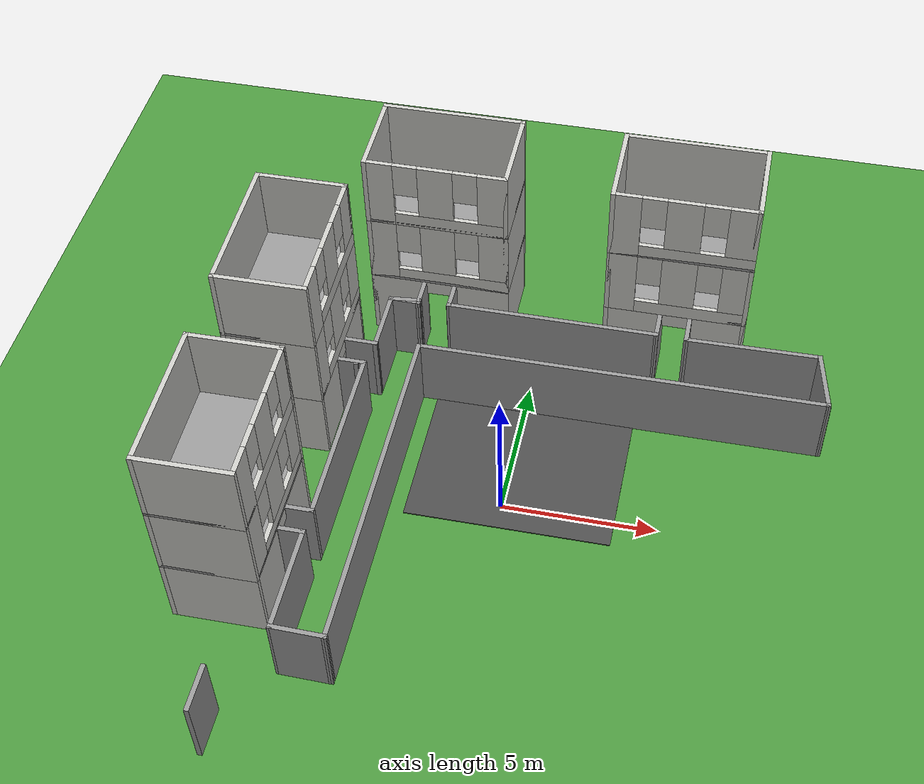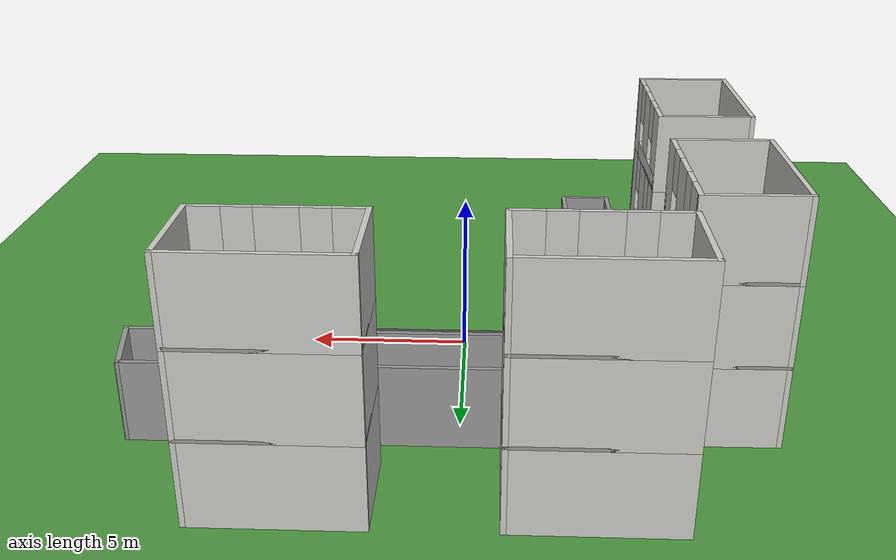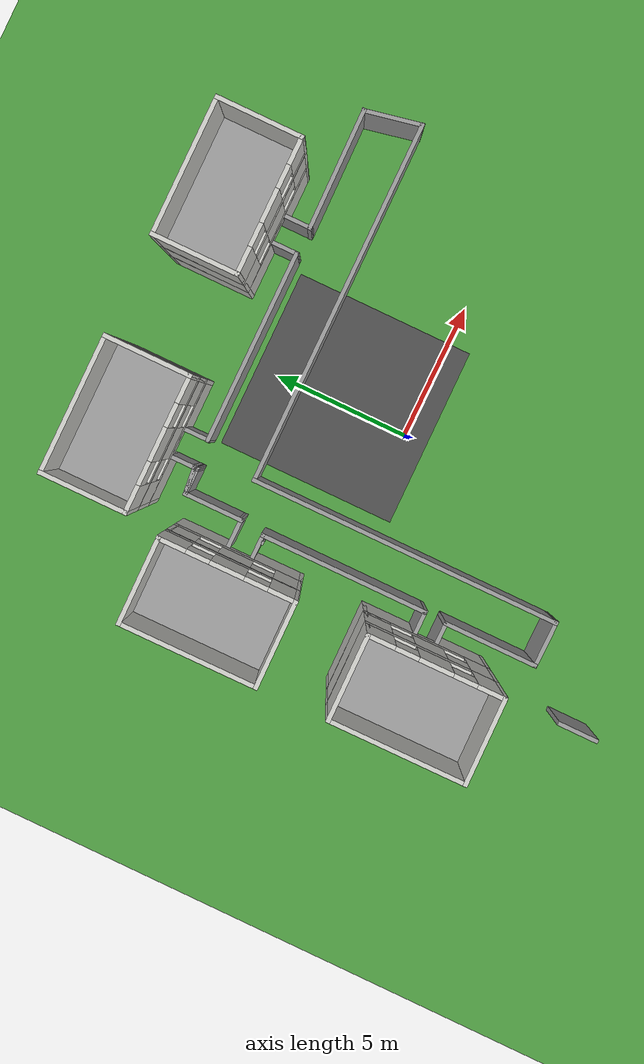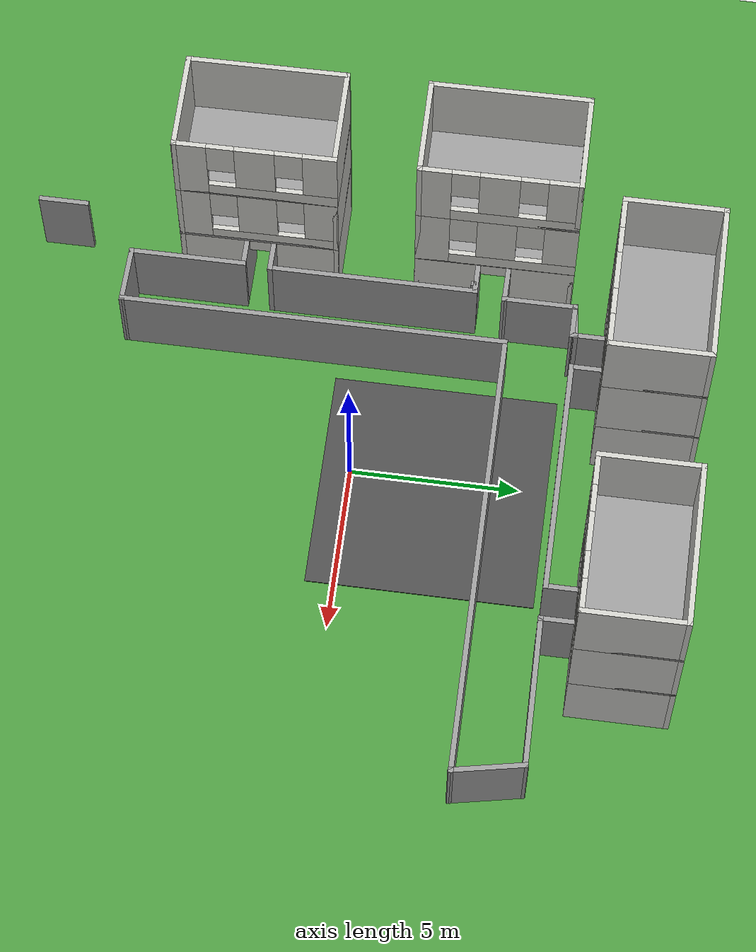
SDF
<sdf version="1.7">
 <world name="default">
  <light name="sun" type="directional">
   <pose>0 0 10 0 -0 0</pose>
   <diffuse>0.8 0.8 0.8 1</diffuse>
   <specular>0.2 0.2 0.2 1</specular>
   <attenuation>
    <range>1000</range>
    <constant>0.9</constant>
    <linear>0.01</linear>
    <quadratic>0.001</quadratic>
   </attenuation>
   <direction>-0.5 0.1 -0.9</direction>
   <spot><inner_angle>0</inner_angle><outer_angle>0</outer_angle><falloff>0</falloff></spot>
  </light>
  <gravity>0 0 -9.8</gravity>
  <magnetic_field>6e-06 2.3e-05 -4.2e-05</magnetic_field>
  <atmosphere type="adiabatic"/>
  <physics type="ode">
   <max_step_size>0.001</max_step_size>
   <real_time_factor>1</real_time_factor>
   <real_time_update_rate>1000</real_time_update_rate>
  </physics>
  <scene><ambient>0.4 0.4 0.4 1</ambient><background>0.7 0.7 0.7 1</background><shadows>1</shadows></scene>
  <audio><device>default</device></audio>
  <model name="ground_plane">
   <static>1</static>
   <link name="link">
    <collision name="collision">
     <geometry><plane><normal>0 0 1</normal><size>100 100</size></plane></geometry>
     <surface><friction><ode><mu>100</mu><mu2>50</mu2></ode></friction></surface>
    </collision>
    <visual name="visual">
     <cast_shadows>0</cast_shadows>
     <geometry><plane><normal>0 0 1</normal><size>100 100</size></plane></geometry>
     <material>
      <script><uri>file://media/materials/scripts/gazebo.material</uri><name>Gazebo/Grass</name></script>
     </material>
    </visual>
   </link>
  </model>
  <spherical_coordinates>
   <surface_model>EARTH_WGS84</surface_model>
   <latitude_deg>0</latitude_deg>
   <longitude_deg>0</longitude_deg>
   <elevation>0</elevation>
   <heading_deg>0</heading_deg>
  </spherical_coordinates>
  <model name="asphalt_plane">
   <static>1</static>
   <link name="link">
    <collision name="collision"><geometry><box><size>6.66663 6.66668 0.033333</size></box></geometry></collision>
    <visual name="visual">
     <cast_shadows>0</cast_shadows>
     <geometry><box><size>6.66663 6.66668 0.033333</size></box></geometry>
     <material>
      <script>
       <uri>model://asphalt_plane/materials/scripts</uri>
       <uri>model://asphalt_plane/materials/textures</uri>
       <name>vrc/asphalt</name>
      </script>
     </material>
    </visual>
   </link>
   <pose>0.322432 2.4947 0 0 -0 0</pose>
  </model>
  <model name="apt">
   <pose>4.4748 8.5092 0 0 -0 0</pose>
   <link name="Floor_10">
    <collision name="Floor_10_Collision">
     <geometry><box><size>4.75 3 0.1</size></box></geometry>
     <pose>0 0 0.05 0 -0 0</pose>
    </collision>
    <visual name="Floor_10_Visual">
     <pose>0 0 0.05 0 -0 0</pose>
     <geometry><box><size>4.75 3 0.1</size></box></geometry>
     <material>
      <script><uri>file://media/materials/scripts/gazebo.material</uri><name>Gazebo/Grey</name></script>
      <ambient>1 1 1 1</ambient>
     </material>
     <meta><layer>2</layer></meta>
    </visual>
    <pose>-0 0 5 0 -0 0</pose>
   </link>
   <link name="Floor_9">
    <collision name="Floor_9_Collision">
     <geometry><box><size>4.75 3 0.1</size></box></geometry>
     <pose>0 0 0.05 0 -0 0</pose>
    </collision>
    <visual name="Floor_9_Visual">
     <pose>0 0 0.05 0 -0 0</pose>
     <geometry><box><size>4.75 3 0.1</size></box></geometry>
     <material>
      <script><uri>file://media/materials/scripts/gazebo.material</uri><name>Gazebo/Grey</name></script>
      <ambient>1 1 1 1</ambient>
     </material>
     <meta><layer>1</layer></meta>
    </visual>
    <pose>-0 0 2.5 0 -0 0</pose>
   </link>
   <link name="Wall_1">
    <collision name="Wall_1_Collision">
     <geometry><box><size>3 0.15 2.5</size></box></geometry>
     <pose>0 0 1.25 0 -0 0</pose>
    </collision>
    <visual name="Wall_1_Visual">
     <pose>0 0 1.25 0 -0 0</pose>
     <geometry><box><size>3 0.15 2.5</size></box></geometry>
     <material>
      <script><uri>file://media/materials/scripts/gazebo.material</uri><name>Gazebo/CeilingTiled</name></script>
      <ambient>1 1 1 1</ambient>
     </material>
     <meta><layer>0</layer></meta>
    </visual>
    <pose>-2.3 0 0 0 -0 -1.5708</pose>
   </link>
   <link name="Wall_2">
    <pose>-0 -1.425 0 0 -0 0</pose>
    <visual name="Wall_2_Visual_0">
     <pose>-1.4125 0 1.25 0 -0 0</pose>
     <geometry><box><size>1.925 0.15 2.5</size></box></geometry>
     <material>
      <script><uri>file://media/materials/scripts/gazebo.material</uri><name>Gazebo/CeilingTiled</name></script>
      <ambient>1 1 1 1</ambient>
     </material>
     <meta><layer>0</layer></meta>
    </visual>
    <collision name="Wall_2_Collision_0">
     <geometry><box><size>1.925 0.15 2.5</size></box></geometry>
     <pose>-1.4125 0 1.25 0 -0 0</pose>
    </collision>
    <visual name="Wall_2_Visual_1">
     <pose>1.4125 0 1.25 0 -0 0</pose>
     <geometry><box><size>1.925 0.15 2.5</size></box></geometry>
     <material>
      <script><uri>file://media/materials/scripts/gazebo.material</uri><name>Gazebo/CeilingTiled</name></script>
      <ambient>1 1 1 1</ambient>
     </material>
     <meta><layer>0</layer></meta>
    </visual>
    <collision name="Wall_2_Collision_1">
     <geometry><box><size>1.925 0.15 2.5</size></box></geometry>
     <pose>1.4125 0 1.25 0 -0 0</pose>
    </collision>
    <visual name="Wall_2_Visual_2">
     <pose>0 0 2.25 0 -0 0</pose>
     <geometry><box><size>0.9 0.15 0.5</size></box></geometry>
     <material>
      <script><uri>file://media/materials/scripts/gazebo.material</uri><name>Gazebo/CeilingTiled</name></script>
      <ambient>1 1 1 1</ambient>
     </material>
     <meta><layer>0</layer></meta>
    </visual>
    <collision name="Wall_2_Collision_2">
     <geometry><box><size>0.9 0.15 0.5</size></box></geometry>
     <pose>0 0 2.25 0 -0 0</pose>
    </collision>
   </link>
   <link name="Wall_3">
    <collision name="Wall_3_Collision">
     <geometry><box><size>3 0.15 2.5</size></box></geometry>
     <pose>0 0 1.25 0 -0 0</pose>
    </collision>
    <visual name="Wall_3_Visual">
     <pose>0 0 1.25 0 -0 0</pose>
     <geometry><box><size>3 0.15 2.5</size></box></geometry>
     <material>
      <script><uri>file://media/materials/scripts/gazebo.material</uri><name>Gazebo/CeilingTiled</name></script>
      <ambient>1 1 1 1</ambient>
     </material>
     <meta><layer>0</layer></meta>
    </visual>
    <pose>2.3 0 0 0 -0 1.5708</pose>
   </link>
   <link name="Wall_4">
    <collision name="Wall_4_Collision">
     <geometry><box><size>4.75 0.15 2.5</size></box></geometry>
     <pose>0 0 1.25 0 -0 0</pose>
    </collision>
    <visual name="Wall_4_Visual">
     <pose>0 0 1.25 0 -0 0</pose>
     <geometry><box><size>4.75 0.15 2.5</size></box></geometry>
     <material>
      <script><uri>file://media/materials/scripts/gazebo.material</uri><name>Gazebo/CeilingTiled</name></script>
      <ambient>1 1 1 1</ambient>
     </material>
     <meta><layer>0</layer></meta>
    </visual>
    <pose>-0 1.425 0 0 -0 3.14159</pose>
   </link>
   <link name="Wall_42">
    <collision name="Wall_42_Collision">
     <geometry><box><size>3 0.15 2.5</size></box></geometry>
     <pose>0 0 1.25 0 -0 0</pose>
    </collision>
    <visual name="Wall_42_Visual">
     <pose>0 0 1.25 0 -0 0</pose>
     <geometry><box><size>3 0.15 2.5</size></box></geometry>
     <material>
      <script><uri>file://media/materials/scripts/gazebo.material</uri><name>Gazebo/CeilingTiled</name></script>
      <ambient>1 1 1 1</ambient>
     </material>
     <meta><layer>1</layer></meta>
    </visual>
    <pose>-2.3 0 2.5 0 -0 -1.5708</pose>
   </link>
   <link name="Wall_43">
    <pose>-0 -1.425 2.5 0 -0 0</pose>
    <visual name="Wall_43_Visual_0">
     <pose>-1.87625 0 1.25 0 -0 0</pose>
     <geometry><box><size>0.9975 0.15 2.5</size></box></geometry>
     <material>
      <script><uri>file://media/materials/scripts/gazebo.material</uri><name>Gazebo/CeilingTiled</name></script>
      <ambient>1 1 1 1</ambient>
     </material>
     <meta><layer>1</layer></meta>
    </visual>
    <collision name="Wall_43_Collision_0">
     <geometry><box><size>0.9975 0.15 2.5</size></box></geometry>
     <pose>-1.87625 0 1.25 0 -0 0</pose>
    </collision>
    <visual name="Wall_43_Visual_1">
     <pose>0.49875 0 0.25 0 -0 0</pose>
     <geometry><box><size>3.7525 0.15 0.5</size></box></geometry>
     <material>
      <script><uri>file://media/materials/scripts/gazebo.material</uri><name>Gazebo/CeilingTiled</name></script>
      <ambient>1 1 1 1</ambient>
     </material>
     <meta><layer>1</layer></meta>
    </visual>
    <collision name="Wall_43_Collision_1">
     <geometry><box><size>3.7525 0.15 0.5</size></box></geometry>
     <pose>0.49875 0 0.25 0 -0 0</pose>
    </collision>
    <visual name="Wall_43_Visual_2">
     <pose>0 0 1.5 0 -0 0</pose>
     <geometry><box><size>1.155 0.15 2</size></box></geometry>
     <material>
      <script><uri>file://media/materials/scripts/gazebo.material</uri><name>Gazebo/CeilingTiled</name></script>
      <ambient>1 1 1 1</ambient>
     </material>
     <meta><layer>1</layer></meta>
    </visual>
    <collision name="Wall_43_Collision_2">
     <geometry><box><size>1.155 0.15 2</size></box></geometry>
     <pose>0 0 1.5 0 -0 0</pose>
    </collision>
    <visual name="Wall_43_Visual_3">
     <pose>1.87625 0 1.5 0 -0 0</pose>
     <geometry><box><size>0.9975 0.15 2</size></box></geometry>
     <material>
      <script><uri>file://media/materials/scripts/gazebo.material</uri><name>Gazebo/CeilingTiled</name></script>
      <ambient>1 1 1 1</ambient>
     </material>
     <meta><layer>1</layer></meta>
    </visual>
    <collision name="Wall_43_Collision_3">
     <geometry><box><size>0.9975 0.15 2</size></box></geometry>
     <pose>1.87625 0 1.5 0 -0 0</pose>
    </collision>
    <visual name="Wall_43_Visual_4">
     <pose>-0.9775 0 1.9 0 -0 0</pose>
     <geometry><box><size>0.8 0.15 1.2</size></box></geometry>
     <material>
      <script><uri>file://media/materials/scripts/gazebo.material</uri><name>Gazebo/CeilingTiled</name></script>
      <ambient>1 1 1 1</ambient>
     </material>
     <meta><layer>1</layer></meta>
    </visual>
    <collision name="Wall_43_Collision_4">
     <geometry><box><size>0.8 0.15 1.2</size></box></geometry>
     <pose>-0.9775 0 1.9 0 -0 0</pose>
    </collision>
    <visual name="Wall_43_Visual_5">
     <pose>0.9775 0 1.9 0 -0 0</pose>
     <geometry><box><size>0.8 0.15 1.2</size></box></geometry>
     <material>
      <script><uri>file://media/materials/scripts/gazebo.material</uri><name>Gazebo/CeilingTiled</name></script>
      <ambient>1 1 1 1</ambient>
     </material>
     <meta><layer>1</layer></meta>
    </visual>
    <collision name="Wall_43_Collision_5">
     <geometry><box><size>0.8 0.15 1.2</size></box></geometry>
     <pose>0.9775 0 1.9 0 -0 0</pose>
    </collision>
   </link>
   <link name="Wall_44">
    <collision name="Wall_44_Collision">
     <geometry><box><size>3 0.15 2.5</size></box></geometry>
     <pose>0 0 1.25 0 -0 0</pose>
    </collision>
    <visual name="Wall_44_Visual">
     <pose>0 0 1.25 0 -0 0</pose>
     <geometry><box><size>3 0.15 2.5</size></box></geometry>
     <material>
      <script><uri>file://media/materials/scripts/gazebo.material</uri><name>Gazebo/CeilingTiled</name></script>
      <ambient>1 1 1 1</ambient>
     </material>
     <meta><layer>1</layer></meta>
    </visual>
    <pose>2.3 0 2.5 0 -0 1.5708</pose>
   </link>
   <link name="Wall_45">
    <collision name="Wall_45_Collision">
     <geometry><box><size>4.75 0.15 2.5</size></box></geometry>
     <pose>0 0 1.25 0 -0 0</pose>
    </collision>
    <visual name="Wall_45_Visual">
     <pose>0 0 1.25 0 -0 0</pose>
     <geometry><box><size>4.75 0.15 2.5</size></box></geometry>
     <material>
      <script><uri>file://media/materials/scripts/gazebo.material</uri><name>Gazebo/CeilingTiled</name></script>
      <ambient>1 1 1 1</ambient>
     </material>
     <meta><layer>1</layer></meta>
    </visual>
    <pose>-0 1.425 2.5 0 -0 3.14159</pose>
   </link>
   <link name="Wall_46">
    <collision name="Wall_46_Collision">
     <geometry><box><size>3 0.15 2.5</size></box></geometry>
     <pose>0 0 1.25 0 -0 0</pose>
    </collision>
    <visual name="Wall_46_Visual">
     <pose>0 0 1.25 0 -0 0</pose>
     <geometry><box><size>3 0.15 2.5</size></box></geometry>
     <material>
      <script><uri>file://media/materials/scripts/gazebo.material</uri><name>Gazebo/CeilingTiled</name></script>
      <ambient>1 1 1 1</ambient>
     </material>
     <meta><layer>2</layer></meta>
    </visual>
    <pose>-2.3 0 5 0 -0 -1.5708</pose>
   </link>
   <link name="Wall_47">
    <pose>-0 -1.425 5 0 -0 0</pose>
    <visual name="Wall_47_Visual_0">
     <pose>-1.87625 0 1.25 0 -0 0</pose>
     <geometry><box><size>0.9975 0.15 2.5</size></box></geometry>
     <material>
      <script><uri>file://media/materials/scripts/gazebo.material</uri><name>Gazebo/CeilingTiled</name></script>
      <ambient>1 1 1 1</ambient>
     </material>
     <meta><layer>2</layer></meta>
    </visual>
    <collision name="Wall_47_Collision_0">
     <geometry><box><size>0.9975 0.15 2.5</size></box></geometry>
     <pose>-1.87625 0 1.25 0 -0 0</pose>
    </collision>
    <visual name="Wall_47_Visual_1">
     <pose>0.49875 0 0.25 0 -0 0</pose>
     <geometry><box><size>3.7525 0.15 0.5</size></box></geometry>
     <material>
      <script><uri>file://media/materials/scripts/gazebo.material</uri><name>Gazebo/CeilingTiled</name></script>
      <ambient>1 1 1 1</ambient>
     </material>
     <meta><layer>2</layer></meta>
    </visual>
    <collision name="Wall_47_Collision_1">
     <geometry><box><size>3.7525 0.15 0.5</size></box></geometry>
     <pose>0.49875 0 0.25 0 -0 0</pose>
    </collision>
    <visual name="Wall_47_Visual_2">
     <pose>0 0 1.5 0 -0 0</pose>
     <geometry><box><size>1.155 0.15 2</size></box></geometry>
     <material>
      <script><uri>file://media/materials/scripts/gazebo.material</uri><name>Gazebo/CeilingTiled</name></script>
      <ambient>1 1 1 1</ambient>
     </material>
     <meta><layer>2</layer></meta>
    </visual>
    <collision name="Wall_47_Collision_2">
     <geometry><box><size>1.155 0.15 2</size></box></geometry>
     <pose>0 0 1.5 0 -0 0</pose>
    </collision>
    <visual name="Wall_47_Visual_3">
     <pose>1.87625 0 1.5 0 -0 0</pose>
     <geometry><box><size>0.9975 0.15 2</size></box></geometry>
     <material>
      <script><uri>file://media/materials/scripts/gazebo.material</uri><name>Gazebo/CeilingTiled</name></script>
      <ambient>1 1 1 1</ambient>
     </material>
     <meta><layer>2</layer></meta>
    </visual>
    <collision name="Wall_47_Collision_3">
     <geometry><box><size>0.9975 0.15 2</size></box></geometry>
     <pose>1.87625 0 1.5 0 -0 0</pose>
    </collision>
    <visual name="Wall_47_Visual_4">
     <pose>-0.9775 0 1.9 0 -0 0</pose>
     <geometry><box><size>0.8 0.15 1.2</size></box></geometry>
     <material>
      <script><uri>file://media/materials/scripts/gazebo.material</uri><name>Gazebo/CeilingTiled</name></script>
      <ambient>1 1 1 1</ambient>
     </material>
     <meta><layer>2</layer></meta>
    </visual>
    <collision name="Wall_47_Collision_4">
     <geometry><box><size>0.8 0.15 1.2</size></box></geometry>
     <pose>-0.9775 0 1.9 0 -0 0</pose>
    </collision>
    <visual name="Wall_47_Visual_5">
     <pose>0.9775 0 1.9 0 -0 0</pose>
     <geometry><box><size>0.8 0.15 1.2</size></box></geometry>
     <material>
      <script><uri>file://media/materials/scripts/gazebo.material</uri><name>Gazebo/CeilingTiled</name></script>
      <ambient>1 1 1 1</ambient>
     </material>
     <meta><layer>2</layer></meta>
    </visual>
    <collision name="Wall_47_Collision_5">
     <geometry><box><size>0.8 0.15 1.2</size></box></geometry>
     <pose>0.9775 0 1.9 0 -0 0</pose>
    </collision>
   </link>
   <link name="Wall_48">
    <collision name="Wall_48_Collision">
     <geometry><box><size>3 0.15 2.5</size></box></geometry>
     <pose>0 0 1.25 0 -0 0</pose>
    </collision>
    <visual name="Wall_48_Visual">
     <pose>0 0 1.25 0 -0 0</pose>
     <geometry><box><size>3 0.15 2.5</size></box></geometry>
     <material>
      <script><uri>file://media/materials/scripts/gazebo.material</uri><name>Gazebo/CeilingTiled</name></script>
      <ambient>1 1 1 1</ambient>
     </material>
     <meta><layer>2</layer></meta>
    </visual>
    <pose>2.3 0 5 0 -0 1.5708</pose>
   </link>
   <link name="Wall_49">
    <collision name="Wall_49_Collision">
     <geometry><box><size>4.75 0.15 2.5</size></box></geometry>
     <pose>0 0 1.25 0 -0 0</pose>
    </collision>
    <visual name="Wall_49_Visual">
     <pose>0 0 1.25 0 -0 0</pose>
     <geometry><box><size>4.75 0.15 2.5</size></box></geometry>
     <material>
      <script><uri>file://media/materials/scripts/gazebo.material</uri><name>Gazebo/CeilingTiled</name></script>
      <ambient>1 1 1 1</ambient>
     </material>
     <meta><layer>2</layer></meta>
    </visual>
    <pose>-0 1.425 5 0 -0 3.14159</pose>
   </link>
   <static>1</static>
  </model>
  <model name="apt_0">
   <pose>-3.52864 8.48149 0 0 -0 0</pose>
   <link name="Floor_10">
    <collision name="Floor_10_Collision">
     <geometry><box><size>4.75 3 0.1</size></box></geometry>
     <pose>0 0 0.05 0 -0 0</pose>
    </collision>
    <visual name="Floor_10_Visual">
     <pose>0 0 0.05 0 -0 0</pose>
     <geometry><box><size>4.75 3 0.1</size></box></geometry>
     <material>
      <script><uri>file://media/materials/scripts/gazebo.material</uri><name>Gazebo/Grey</name></script>
      <ambient>1 1 1 1</ambient>
     </material>
     <meta><layer>2</layer></meta>
    </visual>
    <pose>-0 0 5 0 -0 0</pose>
   </link>
   <link name="Floor_9">
    <collision name="Floor_9_Collision">
     <geometry><box><size>4.75 3 0.1</size></box></geometry>
     <pose>0 0 0.05 0 -0 0</pose>
    </collision>
    <visual name="Floor_9_Visual">
     <pose>0 0 0.05 0 -0 0</pose>
     <geometry><box><size>4.75 3 0.1</size></box></geometry>
     <material>
      <script><uri>file://media/materials/scripts/gazebo.material</uri><name>Gazebo/Grey</name></script>
      <ambient>1 1 1 1</ambient>
     </material>
     <meta><layer>1</layer></meta>
    </visual>
    <pose>-0 0 2.5 0 -0 0</pose>
   </link>
   <link name="Wall_1">
    <collision name="Wall_1_Collision">
     <geometry><box><size>3 0.15 2.5</size></box></geometry>
     <pose>0 0 1.25 0 -0 0</pose>
    </collision>
    <visual name="Wall_1_Visual">
     <pose>0 0 1.25 0 -0 0</pose>
     <geometry><box><size>3 0.15 2.5</size></box></geometry>
     <material>
      <script><uri>file://media/materials/scripts/gazebo.material</uri><name>Gazebo/CeilingTiled</name></script>
      <ambient>1 1 1 1</ambient>
     </material>
     <meta><layer>0</layer></meta>
    </visual>
    <pose>-2.3 0 0 0 -0 -1.5708</pose>
   </link>
   <link name="Wall_2">
    <pose>-0 -1.425 0 0 -0 0</pose>
    <visual name="Wall_2_Visual_0">
     <pose>-1.4125 0 1.25 0 -0 0</pose>
     <geometry><box><size>1.925 0.15 2.5</size></box></geometry>
     <material>
      <script><uri>file://media/materials/scripts/gazebo.material</uri><name>Gazebo/CeilingTiled</name></script>
      <ambient>1 1 1 1</ambient>
     </material>
     <meta><layer>0</layer></meta>
    </visual>
    <collision name="Wall_2_Collision_0">
     <geometry><box><size>1.925 0.15 2.5</size></box></geometry>
     <pose>-1.4125 0 1.25 0 -0 0</pose>
    </collision>
    <visual name="Wall_2_Visual_1">
     <pose>1.4125 0 1.25 0 -0 0</pose>
     <geometry><box><size>1.925 0.15 2.5</size></box></geometry>
     <material>
      <script><uri>file://media/materials/scripts/gazebo.material</uri><name>Gazebo/CeilingTiled</name></script>
      <ambient>1 1 1 1</ambient>
     </material>
     <meta><layer>0</layer></meta>
    </visual>
    <collision name="Wall_2_Collision_1">
     <geometry><box><size>1.925 0.15 2.5</size></box></geometry>
     <pose>1.4125 0 1.25 0 -0 0</pose>
    </collision>
    <visual name="Wall_2_Visual_2">
     <pose>0 0 2.25 0 -0 0</pose>
     <geometry><box><size>0.9 0.15 0.5</size></box></geometry>
     <material>
      <script><uri>file://media/materials/scripts/gazebo.material</uri><name>Gazebo/CeilingTiled</name></script>
      <ambient>1 1 1 1</ambient>
     </material>
     <meta><layer>0</layer></meta>
    </visual>
    <collision name="Wall_2_Collision_2">
     <geometry><box><size>0.9 0.15 0.5</size></box></geometry>
     <pose>0 0 2.25 0 -0 0</pose>
    </collision>
   </link>
   <link name="Wall_3">
    <collision name="Wall_3_Collision">
     <geometry><box><size>3 0.15 2.5</size></box></geometry>
     <pose>0 0 1.25 0 -0 0</pose>
    </collision>
    <visual name="Wall_3_Visual">
     <pose>0 0 1.25 0 -0 0</pose>
     <geometry><box><size>3 0.15 2.5</size></box></geometry>
     <material>
      <script><uri>file://media/materials/scripts/gazebo.material</uri><name>Gazebo/CeilingTiled</name></script>
      <ambient>1 1 1 1</ambient>
     </material>
     <meta><layer>0</layer></meta>
    </visual>
    <pose>2.3 0 0 0 -0 1.5708</pose>
   </link>
   <link name="Wall_4">
    <collision name="Wall_4_Collision">
     <geometry><box><size>4.75 0.15 2.5</size></box></geometry>
     <pose>0 0 1.25 0 -0 0</pose>
    </collision>
    <visual name="Wall_4_Visual">
     <pose>0 0 1.25 0 -0 0</pose>
     <geometry><box><size>4.75 0.15 2.5</size></box></geometry>
     <material>
      <script><uri>file://media/materials/scripts/gazebo.material</uri><name>Gazebo/CeilingTiled</name></script>
      <ambient>1 1 1 1</ambient>
     </material>
     <meta><layer>0</layer></meta>
    </visual>
    <pose>-0 1.425 0 0 -0 3.14159</pose>
   </link>
   <link name="Wall_42">
    <collision name="Wall_42_Collision">
     <geometry><box><size>3 0.15 2.5</size></box></geometry>
     <pose>0 0 1.25 0 -0 0</pose>
    </collision>
    <visual name="Wall_42_Visual">
     <pose>0 0 1.25 0 -0 0</pose>
     <geometry><box><size>3 0.15 2.5</size></box></geometry>
     <material>
      <script><uri>file://media/materials/scripts/gazebo.material</uri><name>Gazebo/CeilingTiled</name></script>
      <ambient>1 1 1 1</ambient>
     </material>
     <meta><layer>1</layer></meta>
    </visual>
    <pose>-2.3 0 2.5 0 -0 -1.5708</pose>
   </link>
   <link name="Wall_43">
    <pose>-0 -1.425 2.5 0 -0 0</pose>
    <visual name="Wall_43_Visual_0">
     <pose>-1.87625 0 1.25 0 -0 0</pose>
     <geometry><box><size>0.9975 0.15 2.5</size></box></geometry>
     <material>
      <script><uri>file://media/materials/scripts/gazebo.material</uri><name>Gazebo/CeilingTiled</name></script>
      <ambient>1 1 1 1</ambient>
     </material>
     <meta><layer>1</layer></meta>
    </visual>
    <collision name="Wall_43_Collision_0">
     <geometry><box><size>0.9975 0.15 2.5</size></box></geometry>
     <pose>-1.87625 0 1.25 0 -0 0</pose>
    </collision>
    <visual name="Wall_43_Visual_1">
     <pose>0.49875 0 0.25 0 -0 0</pose>
     <geometry><box><size>3.7525 0.15 0.5</size></box></geometry>
     <material>
      <script><uri>file://media/materials/scripts/gazebo.material</uri><name>Gazebo/CeilingTiled</name></script>
      <ambient>1 1 1 1</ambient>
     </material>
     <meta><layer>1</layer></meta>
    </visual>
    <collision name="Wall_43_Collision_1">
     <geometry><box><size>3.7525 0.15 0.5</size></box></geometry>
     <pose>0.49875 0 0.25 0 -0 0</pose>
    </collision>
    <visual name="Wall_43_Visual_2">
     <pose>0 0 1.5 0 -0 0</pose>
     <geometry><box><size>1.155 0.15 2</size></box></geometry>
     <material>
      <script><uri>file://media/materials/scripts/gazebo.material</uri><name>Gazebo/CeilingTiled</name></script>
      <ambient>1 1 1 1</ambient>
     </material>
     <meta><layer>1</layer></meta>
    </visual>
    <collision name="Wall_43_Collision_2">
     <geometry><box><size>1.155 0.15 2</size></box></geometry>
     <pose>0 0 1.5 0 -0 0</pose>
    </collision>
    <visual name="Wall_43_Visual_3">
     <pose>1.87625 0 1.5 0 -0 0</pose>
     <geometry><box><size>0.9975 0.15 2</size></box></geometry>
     <material>
      <script><uri>file://media/materials/scripts/gazebo.material</uri><name>Gazebo/CeilingTiled</name></script>
      <ambient>1 1 1 1</ambient>
     </material>
     <meta><layer>1</layer></meta>
    </visual>
    <collision name="Wall_43_Collision_3">
     <geometry><box><size>0.9975 0.15 2</size></box></geometry>
     <pose>1.87625 0 1.5 0 -0 0</pose>
    </collision>
    <visual name="Wall_43_Visual_4">
     <pose>-0.9775 0 1.9 0 -0 0</pose>
     <geometry><box><size>0.8 0.15 1.2</size></box></geometry>
     <material>
      <script><uri>file://media/materials/scripts/gazebo.material</uri><name>Gazebo/CeilingTiled</name></script>
      <ambient>1 1 1 1</ambient>
     </material>
     <meta><layer>1</layer></meta>
    </visual>
    <collision name="Wall_43_Collision_4">
     <geometry><box><size>0.8 0.15 1.2</size></box></geometry>
     <pose>-0.9775 0 1.9 0 -0 0</pose>
    </collision>
    <visual name="Wall_43_Visual_5">
     <pose>0.9775 0 1.9 0 -0 0</pose>
     <geometry><box><size>0.8 0.15 1.2</size></box></geometry>
     <material>
      <script><uri>file://media/materials/scripts/gazebo.material</uri><name>Gazebo/CeilingTiled</name></script>
      <ambient>1 1 1 1</ambient>
     </material>
     <meta><layer>1</layer></meta>
    </visual>
    <collision name="Wall_43_Collision_5">
     <geometry><box><size>0.8 0.15 1.2</size></box></geometry>
     <pose>0.9775 0 1.9 0 -0 0</pose>
    </collision>
   </link>
   <link name="Wall_44">
    <collision name="Wall_44_Collision">
     <geometry><box><size>3 0.15 2.5</size></box></geometry>
     <pose>0 0 1.25 0 -0 0</pose>
    </collision>
    <visual name="Wall_44_Visual">
     <pose>0 0 1.25 0 -0 0</pose>
     <geometry><box><size>3 0.15 2.5</size></box></geometry>
     <material>
      <script><uri>file://media/materials/scripts/gazebo.material</uri><name>Gazebo/CeilingTiled</name></script>
      <ambient>1 1 1 1</ambient>
     </material>
     <meta><layer>1</layer></meta>
    </visual>
    <pose>2.3 0 2.5 0 -0 1.5708</pose>
   </link>
   <link name="Wall_45">
    <collision name="Wall_45_Collision">
     <geometry><box><size>4.75 0.15 2.5</size></box></geometry>
     <pose>0 0 1.25 0 -0 0</pose>
    </collision>
    <visual name="Wall_45_Visual">
     <pose>0 0 1.25 0 -0 0</pose>
     <geometry><box><size>4.75 0.15 2.5</size></box></geometry>
     <material>
      <script><uri>file://media/materials/scripts/gazebo.material</uri><name>Gazebo/CeilingTiled</name></script>
      <ambient>1 1 1 1</ambient>
     </material>
     <meta><layer>1</layer></meta>
    </visual>
    <pose>-0 1.425 2.5 0 -0 3.14159</pose>
   </link>
   <link name="Wall_46">
    <collision name="Wall_46_Collision">
     <geometry><box><size>3 0.15 2.5</size></box></geometry>
     <pose>0 0 1.25 0 -0 0</pose>
    </collision>
    <visual name="Wall_46_Visual">
     <pose>0 0 1.25 0 -0 0</pose>
     <geometry><box><size>3 0.15 2.5</size></box></geometry>
     <material>
      <script><uri>file://media/materials/scripts/gazebo.material</uri><name>Gazebo/CeilingTiled</name></script>
      <ambient>1 1 1 1</ambient>
     </material>
     <meta><layer>2</layer></meta>
    </visual>
    <pose>-2.3 0 5 0 -0 -1.5708</pose>
   </link>
   <link name="Wall_47">
    <pose>-0 -1.425 5 0 -0 0</pose>
    <visual name="Wall_47_Visual_0">
     <pose>-1.87625 0 1.25 0 -0 0</pose>
     <geometry><box><size>0.9975 0.15 2.5</size></box></geometry>
     <material>
      <script><uri>file://media/materials/scripts/gazebo.material</uri><name>Gazebo/CeilingTiled</name></script>
      <ambient>1 1 1 1</ambient>
     </material>
     <meta><layer>2</layer></meta>
    </visual>
    <collision name="Wall_47_Collision_0">
     <geometry><box><size>0.9975 0.15 2.5</size></box></geometry>
     <pose>-1.87625 0 1.25 0 -0 0</pose>
    </collision>
    <visual name="Wall_47_Visual_1">
     <pose>0.49875 0 0.25 0 -0 0</pose>
     <geometry><box><size>3.7525 0.15 0.5</size></box></geometry>
     <material>
      <script><uri>file://media/materials/scripts/gazebo.material</uri><name>Gazebo/CeilingTiled</name></script>
      <ambient>1 1 1 1</ambient>
     </material>
     <meta><layer>2</layer></meta>
    </visual>
    <collision name="Wall_47_Collision_1">
     <geometry><box><size>3.7525 0.15 0.5</size></box></geometry>
     <pose>0.49875 0 0.25 0 -0 0</pose>
    </collision>
    <visual name="Wall_47_Visual_2">
     <pose>0 0 1.5 0 -0 0</pose>
     <geometry><box><size>1.155 0.15 2</size></box></geometry>
     <material>
      <script><uri>file://media/materials/scripts/gazebo.material</uri><name>Gazebo/CeilingTiled</name></script>
      <ambient>1 1 1 1</ambient>
     </material>
     <meta><layer>2</layer></meta>
    </visual>
    <collision name="Wall_47_Collision_2">
     <geometry><box><size>1.155 0.15 2</size></box></geometry>
     <pose>0 0 1.5 0 -0 0</pose>
    </collision>
    <visual name="Wall_47_Visual_3">
     <pose>1.87625 0 1.5 0 -0 0</pose>
     <geometry><box><size>0.9975 0.15 2</size></box></geometry>
     <material>
      <script><uri>file://media/materials/scripts/gazebo.material</uri><name>Gazebo/CeilingTiled</name></script>
      <ambient>1 1 1 1</ambient>
     </material>
     <meta><layer>2</layer></meta>
    </visual>
    <collision name="Wall_47_Collision_3">
     <geometry><box><size>0.9975 0.15 2</size></box></geometry>
     <pose>1.87625 0 1.5 0 -0 0</pose>
    </collision>
    <visual name="Wall_47_Visual_4">
     <pose>-0.9775 0 1.9 0 -0 0</pose>
     <geometry><box><size>0.8 0.15 1.2</size></box></geometry>
     <material>
      <script><uri>file://media/materials/scripts/gazebo.material</uri><name>Gazebo/CeilingTiled</name></script>
      <ambient>1 1 1 1</ambient>
     </material>
     <meta><layer>2</layer></meta>
    </visual>
    <collision name="Wall_47_Collision_4">
     <geometry><box><size>0.8 0.15 1.2</size></box></geometry>
     <pose>-0.9775 0 1.9 0 -0 0</pose>
    </collision>
    <visual name="Wall_47_Visual_5">
     <pose>0.9775 0 1.9 0 -0 0</pose>
     <geometry><box><size>0.8 0.15 1.2</size></box></geometry>
     <material>
      <script><uri>file://media/materials/scripts/gazebo.material</uri><name>Gazebo/CeilingTiled</name></script>
      <ambient>1 1 1 1</ambient>
     </material>
     <meta><layer>2</layer></meta>
    </visual>
    <collision name="Wall_47_Collision_5">
     <geometry><box><size>0.8 0.15 1.2</size></box></geometry>
     <pose>0.9775 0 1.9 0 -0 0</pose>
    </collision>
   </link>
   <link name="Wall_48">
    <collision name="Wall_48_Collision">
     <geometry><box><size>3 0.15 2.5</size></box></geometry>
     <pose>0 0 1.25 0 -0 0</pose>
    </collision>
    <visual name="Wall_48_Visual">
     <pose>0 0 1.25 0 -0 0</pose>
     <geometry><box><size>3 0.15 2.5</size></box></geometry>
     <material>
      <script><uri>file://media/materials/scripts/gazebo.material</uri><name>Gazebo/CeilingTiled</name></script>
      <ambient>1 1 1 1</ambient>
     </material>
     <meta><layer>2</layer></meta>
    </visual>
    <pose>2.3 0 5 0 -0 1.5708</pose>
   </link>
   <link name="Wall_49">
    <collision name="Wall_49_Collision">
     <geometry><box><size>4.75 0.15 2.5</size></box></geometry>
     <pose>0 0 1.25 0 -0 0</pose>
    </collision>
    <visual name="Wall_49_Visual">
     <pose>0 0 1.25 0 -0 0</pose>
     <geometry><box><size>4.75 0.15 2.5</size></box></geometry>
     <material>
      <script><uri>file://media/materials/scripts/gazebo.material</uri><name>Gazebo/CeilingTiled</name></script>
      <ambient>1 1 1 1</ambient>
     </material>
     <meta><layer>2</layer></meta>
    </visual>
    <pose>-0 1.425 5 0 -0 3.14159</pose>
   </link>
   <static>1</static>
  </model>
  <model name="apt_0_clone">
   <pose>-7.51135 3.50237 0 0 -0 1.5769</pose>
   <link name="Floor_10">
    <collision name="Floor_10_Collision">
     <geometry><box><size>4.75 3 0.1</size></box></geometry>
     <pose>0 0 0.05 0 -0 0</pose>
    </collision>
    <visual name="Floor_10_Visual">
     <pose>0 0 0.05 0 -0 0</pose>
     <geometry><box><size>4.75 3 0.1</size></box></geometry>
     <material>
      <script><uri>file://media/materials/scripts/gazebo.material</uri><name>Gazebo/Grey</name></script>
      <ambient>1 1 1 1</ambient>
     </material>
     <meta><layer>2</layer></meta>
    </visual>
    <pose>-0 0 5 0 -0 0</pose>
   </link>
   <link name="Floor_9">
    <collision name="Floor_9_Collision">
     <geometry><box><size>4.75 3 0.1</size></box></geometry>
     <pose>0 0 0.05 0 -0 0</pose>
    </collision>
    <visual name="Floor_9_Visual">
     <pose>0 0 0.05 0 -0 0</pose>
     <geometry><box><size>4.75 3 0.1</size></box></geometry>
     <material>
      <script><uri>file://media/materials/scripts/gazebo.material</uri><name>Gazebo/Grey</name></script>
      <ambient>1 1 1 1</ambient>
     </material>
     <meta><layer>1</layer></meta>
    </visual>
    <pose>-0 0 2.5 0 -0 0</pose>
   </link>
   <link name="Wall_1">
    <collision name="Wall_1_Collision">
     <geometry><box><size>3 0.15 2.5</size></box></geometry>
     <pose>0 0 1.25 0 -0 0</pose>
    </collision>
    <visual name="Wall_1_Visual">
     <pose>0 0 1.25 0 -0 0</pose>
     <geometry><box><size>3 0.15 2.5</size></box></geometry>
     <material>
      <script><uri>file://media/materials/scripts/gazebo.material</uri><name>Gazebo/CeilingTiled</name></script>
      <ambient>1 1 1 1</ambient>
     </material>
     <meta><layer>0</layer></meta>
    </visual>
    <pose>-2.3 0 0 0 -0 -1.5708</pose>
   </link>
   <link name="Wall_2">
    <pose>-0 -1.425 0 0 -0 0</pose>
    <visual name="Wall_2_Visual_0">
     <pose>-1.4125 0 1.25 0 -0 0</pose>
     <geometry><box><size>1.925 0.15 2.5</size></box></geometry>
     <material>
      <script><uri>file://media/materials/scripts/gazebo.material</uri><name>Gazebo/CeilingTiled</name></script>
      <ambient>1 1 1 1</ambient>
     </material>
     <meta><layer>0</layer></meta>
    </visual>
    <collision name="Wall_2_Collision_0">
     <geometry><box><size>1.925 0.15 2.5</size></box></geometry>
     <pose>-1.4125 0 1.25 0 -0 0</pose>
    </collision>
    <visual name="Wall_2_Visual_1">
     <pose>1.4125 0 1.25 0 -0 0</pose>
     <geometry><box><size>1.925 0.15 2.5</size></box></geometry>
     <material>
      <script><uri>file://media/materials/scripts/gazebo.material</uri><name>Gazebo/CeilingTiled</name></script>
      <ambient>1 1 1 1</ambient>
     </material>
     <meta><layer>0</layer></meta>
    </visual>
    <collision name="Wall_2_Collision_1">
     <geometry><box><size>1.925 0.15 2.5</size></box></geometry>
     <pose>1.4125 0 1.25 0 -0 0</pose>
    </collision>
    <visual name="Wall_2_Visual_2">
     <pose>0 0 2.25 0 -0 0</pose>
     <geometry><box><size>0.9 0.15 0.5</size></box></geometry>
     <material>
      <script><uri>file://media/materials/scripts/gazebo.material</uri><name>Gazebo/CeilingTiled</name></script>
      <ambient>1 1 1 1</ambient>
     </material>
     <meta><layer>0</layer></meta>
    </visual>
    <collision name="Wall_2_Collision_2">
     <geometry><box><size>0.9 0.15 0.5</size></box></geometry>
     <pose>0 0 2.25 0 -0 0</pose>
    </collision>
   </link>
   <link name="Wall_3">
    <collision name="Wall_3_Collision">
     <geometry><box><size>3 0.15 2.5</size></box></geometry>
     <pose>0 0 1.25 0 -0 0</pose>
    </collision>
    <visual name="Wall_3_Visual">
     <pose>0 0 1.25 0 -0 0</pose>
     <geometry><box><size>3 0.15 2.5</size></box></geometry>
     <material>
      <script><uri>file://media/materials/scripts/gazebo.material</uri><name>Gazebo/CeilingTiled</name></script>
      <ambient>1 1 1 1</ambient>
     </material>
     <meta><layer>0</layer></meta>
    </visual>
    <pose>2.3 0 0 0 -0 1.5708</pose>
   </link>
   <link name="Wall_4">
    <collision name="Wall_4_Collision">
     <geometry><box><size>4.75 0.15 2.5</size></box></geometry>
     <pose>0 0 1.25 0 -0 0</pose>
    </collision>
    <visual name="Wall_4_Visual">
     <pose>0 0 1.25 0 -0 0</pose>
     <geometry><box><size>4.75 0.15 2.5</size></box></geometry>
     <material>
      <script><uri>file://media/materials/scripts/gazebo.material</uri><name>Gazebo/CeilingTiled</name></script>
      <ambient>1 1 1 1</ambient>
     </material>
     <meta><layer>0</layer></meta>
    </visual>
    <pose>-0 1.425 0 0 -0 3.14159</pose>
   </link>
   <link name="Wall_42">
    <collision name="Wall_42_Collision">
     <geometry><box><size>3 0.15 2.5</size></box></geometry>
     <pose>0 0 1.25 0 -0 0</pose>
    </collision>
    <visual name="Wall_42_Visual">
     <pose>0 0 1.25 0 -0 0</pose>
     <geometry><box><size>3 0.15 2.5</size></box></geometry>
     <material>
      <script><uri>file://media/materials/scripts/gazebo.material</uri><name>Gazebo/CeilingTiled</name></script>
      <ambient>1 1 1 1</ambient>
     </material>
     <meta><layer>1</layer></meta>
    </visual>
    <pose>-2.3 0 2.5 0 -0 -1.5708</pose>
   </link>
   <link name="Wall_43">
    <pose>-0 -1.425 2.5 0 -0 0</pose>
    <visual name="Wall_43_Visual_0">
     <pose>-1.87625 0 1.25 0 -0 0</pose>
     <geometry><box><size>0.9975 0.15 2.5</size></box></geometry>
     <material>
      <script><uri>file://media/materials/scripts/gazebo.material</uri><name>Gazebo/CeilingTiled</name></script>
      <ambient>1 1 1 1</ambient>
     </material>
     <meta><layer>1</layer></meta>
    </visual>
    <collision name="Wall_43_Collision_0">
     <geometry><box><size>0.9975 0.15 2.5</size></box></geometry>
     <pose>-1.87625 0 1.25 0 -0 0</pose>
    </collision>
    <visual name="Wall_43_Visual_1">
     <pose>0.49875 0 0.25 0 -0 0</pose>
     <geometry><box><size>3.7525 0.15 0.5</size></box></geometry>
     <material>
      <script><uri>file://media/materials/scripts/gazebo.material</uri><name>Gazebo/CeilingTiled</name></script>
      <ambient>1 1 1 1</ambient>
     </material>
     <meta><layer>1</layer></meta>
    </visual>
    <collision name="Wall_43_Collision_1">
     <geometry><box><size>3.7525 0.15 0.5</size></box></geometry>
     <pose>0.49875 0 0.25 0 -0 0</pose>
    </collision>
    <visual name="Wall_43_Visual_2">
     <pose>0 0 1.5 0 -0 0</pose>
     <geometry><box><size>1.155 0.15 2</size></box></geometry>
     <material>
      <script><uri>file://media/materials/scripts/gazebo.material</uri><name>Gazebo/CeilingTiled</name></script>
      <ambient>1 1 1 1</ambient>
     </material>
     <meta><layer>1</layer></meta>
    </visual>
    <collision name="Wall_43_Collision_2">
     <geometry><box><size>1.155 0.15 2</size></box></geometry>
     <pose>0 0 1.5 0 -0 0</pose>
    </collision>
    <visual name="Wall_43_Visual_3">
     <pose>1.87625 0 1.5 0 -0 0</pose>
     <geometry><box><size>0.9975 0.15 2</size></box></geometry>
     <material>
      <script><uri>file://media/materials/scripts/gazebo.material</uri><name>Gazebo/CeilingTiled</name></script>
      <ambient>1 1 1 1</ambient>
     </material>
     <meta><layer>1</layer></meta>
    </visual>
    <collision name="Wall_43_Collision_3">
     <geometry><box><size>0.9975 0.15 2</size></box></geometry>
     <pose>1.87625 0 1.5 0 -0 0</pose>
    </collision>
    <visual name="Wall_43_Visual_4">
     <pose>-0.9775 0 1.9 0 -0 0</pose>
     <geometry><box><size>0.8 0.15 1.2</size></box></geometry>
     <material>
      <script><uri>file://media/materials/scripts/gazebo.material</uri><name>Gazebo/CeilingTiled</name></script>
      <ambient>1 1 1 1</ambient>
     </material>
     <meta><layer>1</layer></meta>
    </visual>
    <collision name="Wall_43_Collision_4">
     <geometry><box><size>0.8 0.15 1.2</size></box></geometry>
     <pose>-0.9775 0 1.9 0 -0 0</pose>
    </collision>
    <visual name="Wall_43_Visual_5">
     <pose>0.9775 0 1.9 0 -0 0</pose>
     <geometry><box><size>0.8 0.15 1.2</size></box></geometry>
     <material>
      <script><uri>file://media/materials/scripts/gazebo.material</uri><name>Gazebo/CeilingTiled</name></script>
      <ambient>1 1 1 1</ambient>
     </material>
     <meta><layer>1</layer></meta>
    </visual>
    <collision name="Wall_43_Collision_5">
     <geometry><box><size>0.8 0.15 1.2</size></box></geometry>
     <pose>0.9775 0 1.9 0 -0 0</pose>
    </collision>
   </link>
   <link name="Wall_44">
    <collision name="Wall_44_Collision">
     <geometry><box><size>3 0.15 2.5</size></box></geometry>
     <pose>0 0 1.25 0 -0 0</pose>
    </collision>
    <visual name="Wall_44_Visual">
     <pose>0 0 1.25 0 -0 0</pose>
     <geometry><box><size>3 0.15 2.5</size></box></geometry>
     <material>
      <script><uri>file://media/materials/scripts/gazebo.material</uri><name>Gazebo/CeilingTiled</name></script>
      <ambient>1 1 1 1</ambient>
     </material>
     <meta><layer>1</layer></meta>
    </visual>
    <pose>2.3 0 2.5 0 -0 1.5708</pose>
   </link>
   <link name="Wall_45">
    <collision name="Wall_45_Collision">
     <geometry><box><size>4.75 0.15 2.5</size></box></geometry>
     <pose>0 0 1.25 0 -0 0</pose>
    </collision>
    <visual name="Wall_45_Visual">
     <pose>0 0 1.25 0 -0 0</pose>
     <geometry><box><size>4.75 0.15 2.5</size></box></geometry>
     <material>
      <script><uri>file://media/materials/scripts/gazebo.material</uri><name>Gazebo/CeilingTiled</name></script>
      <ambient>1 1 1 1</ambient>
     </material>
     <meta><layer>1</layer></meta>
    </visual>
    <pose>-0 1.425 2.5 0 -0 3.14159</pose>
   </link>
   <link name="Wall_46">
    <collision name="Wall_46_Collision">
     <geometry><box><size>3 0.15 2.5</size></box></geometry>
     <pose>0 0 1.25 0 -0 0</pose>
    </collision>
    <visual name="Wall_46_Visual">
     <pose>0 0 1.25 0 -0 0</pose>
     <geometry><box><size>3 0.15 2.5</size></box></geometry>
     <material>
      <script><uri>file://media/materials/scripts/gazebo.material</uri><name>Gazebo/CeilingTiled</name></script>
      <ambient>1 1 1 1</ambient>
     </material>
     <meta><layer>2</layer></meta>
    </visual>
    <pose>-2.3 0 5 0 -0 -1.5708</pose>
   </link>
   <link name="Wall_47">
    <pose>-0 -1.425 5 0 -0 0</pose>
    <visual name="Wall_47_Visual_0">
     <pose>-1.87625 0 1.25 0 -0 0</pose>
     <geometry><box><size>0.9975 0.15 2.5</size></box></geometry>
     <material>
      <script><uri>file://media/materials/scripts/gazebo.material</uri><name>Gazebo/CeilingTiled</name></script>
      <ambient>1 1 1 1</ambient>
     </material>
     <meta><layer>2</layer></meta>
    </visual>
    <collision name="Wall_47_Collision_0">
     <geometry><box><size>0.9975 0.15 2.5</size></box></geometry>
     <pose>-1.87625 0 1.25 0 -0 0</pose>
    </collision>
    <visual name="Wall_47_Visual_1">
     <pose>0.49875 0 0.25 0 -0 0</pose>
     <geometry><box><size>3.7525 0.15 0.5</size></box></geometry>
     <material>
      <script><uri>file://media/materials/scripts/gazebo.material</uri><name>Gazebo/CeilingTiled</name></script>
      <ambient>1 1 1 1</ambient>
     </material>
     <meta><layer>2</layer></meta>
    </visual>
    <collision name="Wall_47_Collision_1">
     <geometry><box><size>3.7525 0.15 0.5</size></box></geometry>
     <pose>0.49875 0 0.25 0 -0 0</pose>
    </collision>
    <visual name="Wall_47_Visual_2">
     <pose>0 0 1.5 0 -0 0</pose>
     <geometry><box><size>1.155 0.15 2</size></box></geometry>
     <material>
      <script><uri>file://media/materials/scripts/gazebo.material</uri><name>Gazebo/CeilingTiled</name></script>
      <ambient>1 1 1 1</ambient>
     </material>
     <meta><layer>2</layer></meta>
    </visual>
    <collision name="Wall_47_Collision_2">
     <geometry><box><size>1.155 0.15 2</size></box></geometry>
     <pose>0 0 1.5 0 -0 0</pose>
    </collision>
    <visual name="Wall_47_Visual_3">
     <pose>1.87625 0 1.5 0 -0 0</pose>
     <geometry><box><size>0.9975 0.15 2</size></box></geometry>
     <material>
      <script><uri>file://media/materials/scripts/gazebo.material</uri><name>Gazebo/CeilingTiled</name></script>
      <ambient>1 1 1 1</ambient>
     </material>
     <meta><layer>2</layer></meta>
    </visual>
    <collision name="Wall_47_Collision_3">
     <geometry><box><size>0.9975 0.15 2</size></box></geometry>
     <pose>1.87625 0 1.5 0 -0 0</pose>
    </collision>
    <visual name="Wall_47_Visual_4">
     <pose>-0.9775 0 1.9 0 -0 0</pose>
     <geometry><box><size>0.8 0.15 1.2</size></box></geometry>
     <material>
      <script><uri>file://media/materials/scripts/gazebo.material</uri><name>Gazebo/CeilingTiled</name></script>
      <ambient>1 1 1 1</ambient>
     </material>
     <meta><layer>2</layer></meta>
    </visual>
    <collision name="Wall_47_Collision_4">
     <geometry><box><size>0.8 0.15 1.2</size></box></geometry>
     <pose>-0.9775 0 1.9 0 -0 0</pose>
    </collision>
    <visual name="Wall_47_Visual_5">
     <pose>0.9775 0 1.9 0 -0 0</pose>
     <geometry><box><size>0.8 0.15 1.2</size></box></geometry>
     <material>
      <script><uri>file://media/materials/scripts/gazebo.material</uri><name>Gazebo/CeilingTiled</name></script>
      <ambient>1 1 1 1</ambient>
     </material>
     <meta><layer>2</layer></meta>
    </visual>
    <collision name="Wall_47_Collision_5">
     <geometry><box><size>0.8 0.15 1.2</size></box></geometry>
     <pose>0.9775 0 1.9 0 -0 0</pose>
    </collision>
   </link>
   <link name="Wall_48">
    <collision name="Wall_48_Collision">
     <geometry><box><size>3 0.15 2.5</size></box></geometry>
     <pose>0 0 1.25 0 -0 0</pose>
    </collision>
    <visual name="Wall_48_Visual">
     <pose>0 0 1.25 0 -0 0</pose>
     <geometry><box><size>3 0.15 2.5</size></box></geometry>
     <material>
      <script><uri>file://media/materials/scripts/gazebo.material</uri><name>Gazebo/CeilingTiled</name></script>
      <ambient>1 1 1 1</ambient>
     </material>
     <meta><layer>2</layer></meta>
    </visual>
    <pose>2.3 0 5 0 -0 1.5708</pose>
   </link>
   <link name="Wall_49">
    <collision name="Wall_49_Collision">
     <geometry><box><size>4.75 0.15 2.5</size></box></geometry>
     <pose>0 0 1.25 0 -0 0</pose>
    </collision>
    <visual name="Wall_49_Visual">
     <pose>0 0 1.25 0 -0 0</pose>
     <geometry><box><size>4.75 0.15 2.5</size></box></geometry>
     <material>
      <script><uri>file://media/materials/scripts/gazebo.material</uri><name>Gazebo/CeilingTiled</name></script>
      <ambient>1 1 1 1</ambient>
     </material>
     <meta><layer>2</layer></meta>
    </visual>
    <pose>-0 1.425 5 0 -0 3.14159</pose>
   </link>
   <static>1</static>
  </model>
  <model name="apt_0_clone_clone">
   <pose>-7.45101 -3.51166 0 0 -0 1.5769</pose>
   <link name="Floor_10">
    <collision name="Floor_10_Collision">
     <geometry><box><size>4.75 3 0.1</size></box></geometry>
     <pose>0 0 0.05 0 -0 0</pose>
    </collision>
    <visual name="Floor_10_Visual">
     <pose>0 0 0.05 0 -0 0</pose>
     <geometry><box><size>4.75 3 0.1</size></box></geometry>
     <material>
      <script><uri>file://media/materials/scripts/gazebo.material</uri><name>Gazebo/Grey</name></script>
      <ambient>1 1 1 1</ambient>
     </material>
     <meta><layer>2</layer></meta>
    </visual>
    <pose>-0 0 5 0 -0 0</pose>
   </link>
   <link name="Floor_9">
    <collision name="Floor_9_Collision">
     <geometry><box><size>4.75 3 0.1</size></box></geometry>
     <pose>0 0 0.05 0 -0 0</pose>
    </collision>
    <visual name="Floor_9_Visual">
     <pose>0 0 0.05 0 -0 0</pose>
     <geometry><box><size>4.75 3 0.1</size></box></geometry>
     <material>
      <script><uri>file://media/materials/scripts/gazebo.material</uri><name>Gazebo/Grey</name></script>
      <ambient>1 1 1 1</ambient>
     </material>
     <meta><layer>1</layer></meta>
    </visual>
    <pose>-0 0 2.5 0 -0 0</pose>
   </link>
   <link name="Wall_1">
    <collision name="Wall_1_Collision">
     <geometry><box><size>3 0.15 2.5</size></box></geometry>
     <pose>0 0 1.25 0 -0 0</pose>
    </collision>
    <visual name="Wall_1_Visual">
     <pose>0 0 1.25 0 -0 0</pose>
     <geometry><box><size>3 0.15 2.5</size></box></geometry>
     <material>
      <script><uri>file://media/materials/scripts/gazebo.material</uri><name>Gazebo/CeilingTiled</name></script>
      <ambient>1 1 1 1</ambient>
     </material>
     <meta><layer>0</layer></meta>
    </visual>
    <pose>-2.3 0 0 0 -0 -1.5708</pose>
   </link>
   <link name="Wall_2">
    <pose>-0 -1.425 0 0 -0 0</pose>
    <visual name="Wall_2_Visual_0">
     <pose>-1.4125 0 1.25 0 -0 0</pose>
     <geometry><box><size>1.925 0.15 2.5</size></box></geometry>
     <material>
      <script><uri>file://media/materials/scripts/gazebo.material</uri><name>Gazebo/CeilingTiled</name></script>
      <ambient>1 1 1 1</ambient>
     </material>
     <meta><layer>0</layer></meta>
    </visual>
    <collision name="Wall_2_Collision_0">
     <geometry><box><size>1.925 0.15 2.5</size></box></geometry>
     <pose>-1.4125 0 1.25 0 -0 0</pose>
    </collision>
    <visual name="Wall_2_Visual_1">
     <pose>1.4125 0 1.25 0 -0 0</pose>
     <geometry><box><size>1.925 0.15 2.5</size></box></geometry>
     <material>
      <script><uri>file://media/materials/scripts/gazebo.material</uri><name>Gazebo/CeilingTiled</name></script>
      <ambient>1 1 1 1</ambient>
     </material>
     <meta><layer>0</layer></meta>
    </visual>
    <collision name="Wall_2_Collision_1">
     <geometry><box><size>1.925 0.15 2.5</size></box></geometry>
     <pose>1.4125 0 1.25 0 -0 0</pose>
    </collision>
    <visual name="Wall_2_Visual_2">
     <pose>0 0 2.25 0 -0 0</pose>
     <geometry><box><size>0.9 0.15 0.5</size></box></geometry>
     <material>
      <script><uri>file://media/materials/scripts/gazebo.material</uri><name>Gazebo/CeilingTiled</name></script>
      <ambient>1 1 1 1</ambient>
     </material>
     <meta><layer>0</layer></meta>
    </visual>
    <collision name="Wall_2_Collision_2">
     <geometry><box><size>0.9 0.15 0.5</size></box></geometry>
     <pose>0 0 2.25 0 -0 0</pose>
    </collision>
   </link>
   <link name="Wall_3">
    <collision name="Wall_3_Collision">
     <geometry><box><size>3 0.15 2.5</size></box></geometry>
     <pose>0 0 1.25 0 -0 0</pose>
    </collision>
    <visual name="Wall_3_Visual">
     <pose>0 0 1.25 0 -0 0</pose>
     <geometry><box><size>3 0.15 2.5</size></box></geometry>
     <material>
      <script><uri>file://media/materials/scripts/gazebo.material</uri><name>Gazebo/CeilingTiled</name></script>
      <ambient>1 1 1 1</ambient>
     </material>
     <meta><layer>0</layer></meta>
    </visual>
    <pose>2.3 0 0 0 -0 1.5708</pose>
   </link>
   <link name="Wall_4">
    <collision name="Wall_4_Collision">
     <geometry><box><size>4.75 0.15 2.5</size></box></geometry>
     <pose>0 0 1.25 0 -0 0</pose>
    </collision>
    <visual name="Wall_4_Visual">
     <pose>0 0 1.25 0 -0 0</pose>
     <geometry><box><size>4.75 0.15 2.5</size></box></geometry>
     <material>
      <script><uri>file://media/materials/scripts/gazebo.material</uri><name>Gazebo/CeilingTiled</name></script>
      <ambient>1 1 1 1</ambient>
     </material>
     <meta><layer>0</layer></meta>
    </visual>
    <pose>-0 1.425 0 0 -0 3.14159</pose>
   </link>
   <link name="Wall_42">
    <collision name="Wall_42_Collision">
     <geometry><box><size>3 0.15 2.5</size></box></geometry>
     <pose>0 0 1.25 0 -0 0</pose>
    </collision>
    <visual name="Wall_42_Visual">
     <pose>0 0 1.25 0 -0 0</pose>
     <geometry><box><size>3 0.15 2.5</size></box></geometry>
     <material>
      <script><uri>file://media/materials/scripts/gazebo.material</uri><name>Gazebo/CeilingTiled</name></script>
      <ambient>1 1 1 1</ambient>
     </material>
     <meta><layer>1</layer></meta>
    </visual>
    <pose>-2.3 0 2.5 0 -0 -1.5708</pose>
   </link>
   <link name="Wall_43">
    <pose>-0 -1.425 2.5 0 -0 0</pose>
    <visual name="Wall_43_Visual_0">
     <pose>-1.87625 0 1.25 0 -0 0</pose>
     <geometry><box><size>0.9975 0.15 2.5</size></box></geometry>
     <material>
      <script><uri>file://media/materials/scripts/gazebo.material</uri><name>Gazebo/CeilingTiled</name></script>
      <ambient>1 1 1 1</ambient>
     </material>
     <meta><layer>1</layer></meta>
    </visual>
    <collision name="Wall_43_Collision_0">
     <geometry><box><size>0.9975 0.15 2.5</size></box></geometry>
     <pose>-1.87625 0 1.25 0 -0 0</pose>
    </collision>
    <visual name="Wall_43_Visual_1">
     <pose>0.49875 0 0.25 0 -0 0</pose>
     <geometry><box><size>3.7525 0.15 0.5</size></box></geometry>
     <material>
      <script><uri>file://media/materials/scripts/gazebo.material</uri><name>Gazebo/CeilingTiled</name></script>
      <ambient>1 1 1 1</ambient>
     </material>
     <meta><layer>1</layer></meta>
    </visual>
    <collision name="Wall_43_Collision_1">
     <geometry><box><size>3.7525 0.15 0.5</size></box></geometry>
     <pose>0.49875 0 0.25 0 -0 0</pose>
    </collision>
    <visual name="Wall_43_Visual_2">
     <pose>0 0 1.5 0 -0 0</pose>
     <geometry><box><size>1.155 0.15 2</size></box></geometry>
     <material>
      <script><uri>file://media/materials/scripts/gazebo.material</uri><name>Gazebo/CeilingTiled</name></script>
      <ambient>1 1 1 1</ambient>
     </material>
     <meta><layer>1</layer></meta>
    </visual>
    <collision name="Wall_43_Collision_2">
     <geometry><box><size>1.155 0.15 2</size></box></geometry>
     <pose>0 0 1.5 0 -0 0</pose>
    </collision>
    <visual name="Wall_43_Visual_3">
     <pose>1.87625 0 1.5 0 -0 0</pose>
     <geometry><box><size>0.9975 0.15 2</size></box></geometry>
     <material>
      <script><uri>file://media/materials/scripts/gazebo.material</uri><name>Gazebo/CeilingTiled</name></script>
      <ambient>1 1 1 1</ambient>
     </material>
     <meta><layer>1</layer></meta>
    </visual>
    <collision name="Wall_43_Collision_3">
     <geometry><box><size>0.9975 0.15 2</size></box></geometry>
     <pose>1.87625 0 1.5 0 -0 0</pose>
    </collision>
    <visual name="Wall_43_Visual_4">
     <pose>-0.9775 0 1.9 0 -0 0</pose>
     <geometry><box><size>0.8 0.15 1.2</size></box></geometry>
     <material>
      <script><uri>file://media/materials/scripts/gazebo.material</uri><name>Gazebo/CeilingTiled</name></script>
      <ambient>1 1 1 1</ambient>
     </material>
     <meta><layer>1</layer></meta>
    </visual>
    <collision name="Wall_43_Collision_4">
     <geometry><box><size>0.8 0.15 1.2</size></box></geometry>
     <pose>-0.9775 0 1.9 0 -0 0</pose>
    </collision>
    <visual name="Wall_43_Visual_5">
     <pose>0.9775 0 1.9 0 -0 0</pose>
     <geometry><box><size>0.8 0.15 1.2</size></box></geometry>
     <material>
      <script><uri>file://media/materials/scripts/gazebo.material</uri><name>Gazebo/CeilingTiled</name></script>
      <ambient>1 1 1 1</ambient>
     </material>
     <meta><layer>1</layer></meta>
    </visual>
    <collision name="Wall_43_Collision_5">
     <geometry><box><size>0.8 0.15 1.2</size></box></geometry>
     <pose>0.9775 0 1.9 0 -0 0</pose>
    </collision>
   </link>
   <link name="Wall_44">
    <collision name="Wall_44_Collision">
     <geometry><box><size>3 0.15 2.5</size></box></geometry>
     <pose>0 0 1.25 0 -0 0</pose>
    </collision>
    <visual name="Wall_44_Visual">
     <pose>0 0 1.25 0 -0 0</pose>
     <geometry><box><size>3 0.15 2.5</size></box></geometry>
     <material>
      <script><uri>file://media/materials/scripts/gazebo.material</uri><name>Gazebo/CeilingTiled</name></script>
      <ambient>1 1 1 1</ambient>
     </material>
     <meta><layer>1</layer></meta>
    </visual>
    <pose>2.3 0 2.5 0 -0 1.5708</pose>
   </link>
   <link name="Wall_45">
    <collision name="Wall_45_Collision">
     <geometry><box><size>4.75 0.15 2.5</size></box></geometry>
     <pose>0 0 1.25 0 -0 0</pose>
    </collision>
    <visual name="Wall_45_Visual">
     <pose>0 0 1.25 0 -0 0</pose>
     <geometry><box><size>4.75 0.15 2.5</size></box></geometry>
     <material>
      <script><uri>file://media/materials/scripts/gazebo.material</uri><name>Gazebo/CeilingTiled</name></script>
      <ambient>1 1 1 1</ambient>
     </material>
     <meta><layer>1</layer></meta>
    </visual>
    <pose>-0 1.425 2.5 0 -0 3.14159</pose>
   </link>
   <link name="Wall_46">
    <collision name="Wall_46_Collision">
     <geometry><box><size>3 0.15 2.5</size></box></geometry>
     <pose>0 0 1.25 0 -0 0</pose>
    </collision>
    <visual name="Wall_46_Visual">
     <pose>0 0 1.25 0 -0 0</pose>
     <geometry><box><size>3 0.15 2.5</size></box></geometry>
     <material>
      <script><uri>file://media/materials/scripts/gazebo.material</uri><name>Gazebo/CeilingTiled</name></script>
      <ambient>1 1 1 1</ambient>
     </material>
     <meta><layer>2</layer></meta>
    </visual>
    <pose>-2.3 0 5 0 -0 -1.5708</pose>
   </link>
   <link name="Wall_47">
    <pose>-0 -1.425 5 0 -0 0</pose>
    <visual name="Wall_47_Visual_0">
     <pose>-1.87625 0 1.25 0 -0 0</pose>
     <geometry><box><size>0.9975 0.15 2.5</size></box></geometry>
     <material>
      <script><uri>file://media/materials/scripts/gazebo.material</uri><name>Gazebo/CeilingTiled</name></script>
      <ambient>1 1 1 1</ambient>
     </material>
     <meta><layer>2</layer></meta>
    </visual>
    <collision name="Wall_47_Collision_0">
     <geometry><box><size>0.9975 0.15 2.5</size></box></geometry>
     <pose>-1.87625 0 1.25 0 -0 0</pose>
    </collision>
    <visual name="Wall_47_Visual_1">
     <pose>0.49875 0 0.25 0 -0 0</pose>
     <geometry><box><size>3.7525 0.15 0.5</size></box></geometry>
     <material>
      <script><uri>file://media/materials/scripts/gazebo.material</uri><name>Gazebo/CeilingTiled</name></script>
      <ambient>1 1 1 1</ambient>
     </material>
     <meta><layer>2</layer></meta>
    </visual>
    <collision name="Wall_47_Collision_1">
     <geometry><box><size>3.7525 0.15 0.5</size></box></geometry>
     <pose>0.49875 0 0.25 0 -0 0</pose>
    </collision>
    <visual name="Wall_47_Visual_2">
     <pose>0 0 1.5 0 -0 0</pose>
     <geometry><box><size>1.155 0.15 2</size></box></geometry>
     <material>
      <script><uri>file://media/materials/scripts/gazebo.material</uri><name>Gazebo/CeilingTiled</name></script>
      <ambient>1 1 1 1</ambient>
     </material>
     <meta><layer>2</layer></meta>
    </visual>
    <collision name="Wall_47_Collision_2">
     <geometry><box><size>1.155 0.15 2</size></box></geometry>
     <pose>0 0 1.5 0 -0 0</pose>
    </collision>
    <visual name="Wall_47_Visual_3">
     <pose>1.87625 0 1.5 0 -0 0</pose>
     <geometry><box><size>0.9975 0.15 2</size></box></geometry>
     <material>
      <script><uri>file://media/materials/scripts/gazebo.material</uri><name>Gazebo/CeilingTiled</name></script>
      <ambient>1 1 1 1</ambient>
     </material>
     <meta><layer>2</layer></meta>
    </visual>
    <collision name="Wall_47_Collision_3">
     <geometry><box><size>0.9975 0.15 2</size></box></geometry>
     <pose>1.87625 0 1.5 0 -0 0</pose>
    </collision>
    <visual name="Wall_47_Visual_4">
     <pose>-0.9775 0 1.9 0 -0 0</pose>
     <geometry><box><size>0.8 0.15 1.2</size></box></geometry>
     <material>
      <script><uri>file://media/materials/scripts/gazebo.material</uri><name>Gazebo/CeilingTiled</name></script>
      <ambient>1 1 1 1</ambient>
     </material>
     <meta><layer>2</layer></meta>
    </visual>
    <collision name="Wall_47_Collision_4">
     <geometry><box><size>0.8 0.15 1.2</size></box></geometry>
     <pose>-0.9775 0 1.9 0 -0 0</pose>
    </collision>
    <visual name="Wall_47_Visual_5">
     <pose>0.9775 0 1.9 0 -0 0</pose>
     <geometry><box><size>0.8 0.15 1.2</size></box></geometry>
     <material>
      <script><uri>file://media/materials/scripts/gazebo.material</uri><name>Gazebo/CeilingTiled</name></script>
      <ambient>1 1 1 1</ambient>
     </material>
     <meta><layer>2</layer></meta>
    </visual>
    <collision name="Wall_47_Collision_5">
     <geometry><box><size>0.8 0.15 1.2</size></box></geometry>
     <pose>0.9775 0 1.9 0 -0 0</pose>
    </collision>
   </link>
   <link name="Wall_48">
    <collision name="Wall_48_Collision">
     <geometry><box><size>3 0.15 2.5</size></box></geometry>
     <pose>0 0 1.25 0 -0 0</pose>
    </collision>
    <visual name="Wall_48_Visual">
     <pose>0 0 1.25 0 -0 0</pose>
     <geometry><box><size>3 0.15 2.5</size></box></geometry>
     <material>
      <script><uri>file://media/materials/scripts/gazebo.material</uri><name>Gazebo/CeilingTiled</name></script>
      <ambient>1 1 1 1</ambient>
     </material>
     <meta><layer>2</layer></meta>
    </visual>
    <pose>2.3 0 5 0 -0 1.5708</pose>
   </link>
   <link name="Wall_49">
    <collision name="Wall_49_Collision">
     <geometry><box><size>4.75 0.15 2.5</size></box></geometry>
     <pose>0 0 1.25 0 -0 0</pose>
    </collision>
    <visual name="Wall_49_Visual">
     <pose>0 0 1.25 0 -0 0</pose>
     <geometry><box><size>4.75 0.15 2.5</size></box></geometry>
     <material>
      <script><uri>file://media/materials/scripts/gazebo.material</uri><name>Gazebo/CeilingTiled</name></script>
      <ambient>1 1 1 1</ambient>
     </material>
     <meta><layer>2</layer></meta>
    </visual>
    <pose>-0 1.425 5 0 -0 3.14159</pose>
   </link>
   <static>1</static>
  </model>
  <model name="mypath">
   <pose>1.50454 -1.24093 0 0 -0 0</pose>
   <link name="Wall_102">
    <collision name="Wall_102_Collision">
     <geometry><box><size>1 0.15 2.5</size></box></geometry>
     <pose>0 0 1.25 0 -0 0</pose>
    </collision>
    <visual name="Wall_102_Visual">
     <pose>0 0 1.25 0 -0 0</pose>
     <geometry><box><size>1 0.15 2.5</size></box></geometry>
     <material>
      <script><uri>file://media/materials/scripts/gazebo.material</uri><name>Gazebo/Grey</name></script>
      <ambient>1 1 1 1</ambient>
     </material>
     <meta><layer>0</layer></meta>
    </visual>
    <pose>-7.07012 4.27652 0 0 -0 0</pose>
   </link>
   <link name="Wall_103">
    <collision name="Wall_103_Collision">
     <geometry><box><size>6.25 0.15 2.5</size></box></geometry>
     <pose>0 0 1.25 0 -0 0</pose>
    </collision>
    <visual name="Wall_103_Visual">
     <pose>0 0 1.25 0 -0 0</pose>
     <geometry><box><size>6.25 0.15 2.5</size></box></geometry>
     <material>
      <script><uri>file://media/materials/scripts/gazebo.material</uri><name>Gazebo/Grey</name></script>
      <ambient>1 1 1 1</ambient>
     </material>
     <meta><layer>0</layer></meta>
    </visual>
    <pose>-6.64512 1.22652 0 0 -0 -1.5708</pose>
   </link>
   <link name="Wall_104">
    <collision name="Wall_104_Collision">
     <geometry><box><size>1.75 0.15 2.5</size></box></geometry>
     <pose>0 0 1.25 0 -0 0</pose>
    </collision>
    <visual name="Wall_104_Visual">
     <pose>0 0 1.25 0 -0 0</pose>
     <geometry><box><size>1.75 0.15 2.5</size></box></geometry>
     <material>
      <script><uri>file://media/materials/scripts/gazebo.material</uri><name>Gazebo/Grey</name></script>
      <ambient>1 1 1 1</ambient>
     </material>
     <meta><layer>0</layer></meta>
    </visual>
    <pose>-7.44512 -1.82348 0 0 -0 3.14159</pose>
   </link>
   <link name="Wall_107">
    <collision name="Wall_107_Collision">
     <geometry><box><size>1.75 0.15 2.5</size></box></geometry>
     <pose>0 0 1.25 0 -0 0</pose>
    </collision>
    <visual name="Wall_107_Visual">
     <pose>0 0 1.25 0 -0 0</pose>
     <geometry><box><size>1.75 0.15 2.5</size></box></geometry>
     <material>
      <script><uri>file://media/materials/scripts/gazebo.material</uri><name>Gazebo/Grey</name></script>
      <ambient>1 1 1 1</ambient>
     </material>
     <meta><layer>0</layer></meta>
    </visual>
    <pose>-7.48818 -2.62602 0 0 -0 0</pose>
   </link>
   <link name="Wall_109">
    <collision name="Wall_109_Collision">
     <geometry><box><size>3.5 0.15 2.5</size></box></geometry>
     <pose>0 0 1.25 0 -0 0</pose>
    </collision>
    <visual name="Wall_109_Visual">
     <pose>0 0 1.25 0 -0 0</pose>
     <geometry><box><size>3.5 0.15 2.5</size></box></geometry>
     <material>
      <script><uri>file://media/materials/scripts/gazebo.material</uri><name>Gazebo/Grey</name></script>
      <ambient>1 1 1 1</ambient>
     </material>
     <meta><layer>0</layer></meta>
    </visual>
    <pose>-6.68818 -4.30102 0 0 -0 -1.5708</pose>
   </link>
   <link name="Wall_110">
    <collision name="Wall_110_Collision">
     <geometry><box><size>1.76327 0.15 2.5</size></box></geometry>
     <pose>0 0 1.25 0 -0 0</pose>
    </collision>
    <visual name="Wall_110_Visual">
     <pose>0 0 1.25 0 -0 0</pose>
     <geometry><box><size>1.76327 0.15 2.5</size></box></geometry>
     <material>
      <script><uri>file://media/materials/scripts/gazebo.material</uri><name>Gazebo/Grey</name></script>
      <ambient>1 1 1 1</ambient>
     </material>
     <meta><layer>0</layer></meta>
    </visual>
    <pose>-5.88167 -5.99034 0 0 -0 -0.017755</pose>
   </link>
   <link name="Wall_115">
    <collision name="Wall_115_Collision">
     <geometry><box><size>0.15 0.15 2.5</size></box></geometry>
     <pose>0 0 1.25 0 -0 0</pose>
    </collision>
    <visual name="Wall_115_Visual">
     <pose>0 0 1.25 0 -0 0</pose>
     <geometry><box><size>0.15 0.15 2.5</size></box></geometry>
     <material>
      <script><uri>file://media/materials/scripts/gazebo.material</uri><name>Gazebo/Grey</name></script>
      <ambient>1 1 1 1</ambient>
     </material>
     <meta><layer>0</layer></meta>
    </visual>
    <pose>-5.547 7.36058 0 0 -0 0</pose>
   </link>
   <link name="Wall_117">
    <collision name="Wall_117_Collision">
     <geometry><box><size>1 0.15 2.5</size></box></geometry>
     <pose>0 0 1.25 0 -0 0</pose>
    </collision>
    <visual name="Wall_117_Visual">
     <pose>0 0 1.25 0 -0 0</pose>
     <geometry><box><size>1 0.15 2.5</size></box></geometry>
     <material>
      <script><uri>file://media/materials/scripts/gazebo.material</uri><name>Gazebo/Grey</name></script>
      <ambient>1 1 1 1</ambient>
     </material>
     <meta><layer>0</layer></meta>
    </visual>
    <pose>-5.55272 7.78558 0 0 -0 1.5708</pose>
   </link>
   <link name="Wall_120">
    <collision name="Wall_120_Collision">
     <geometry><box><size>1.09461 0.15 2.5</size></box></geometry>
     <pose>0 0 1.25 0 -0 0</pose>
    </collision>
    <visual name="Wall_120_Visual">
     <pose>0 0 1.25 0 -0 0</pose>
     <geometry><box><size>1.09461 0.15 2.5</size></box></geometry>
     <material>
      <script><uri>file://media/materials/scripts/gazebo.material</uri><name>Gazebo/Grey</name></script>
      <ambient>1 1 1 1</ambient>
     </material>
     <meta><layer>0</layer></meta>
    </visual>
    <pose>-6.02249 7.31176 0 0 -0 0.103556</pose>
   </link>
   <link name="Wall_121">
    <collision name="Wall_121_Collision">
     <geometry><box><size>0.25 0.15 2.5</size></box></geometry>
     <pose>0 0 1.25 0 -0 0</pose>
    </collision>
    <visual name="Wall_121_Visual">
     <pose>0 0 1.25 0 -0 0</pose>
     <geometry><box><size>0.25 0.15 2.5</size></box></geometry>
     <material>
      <script><uri>file://media/materials/scripts/gazebo.material</uri><name>Gazebo/Grey</name></script>
      <ambient>1 1 1 1</ambient>
     </material>
     <meta><layer>0</layer></meta>
    </visual>
    <pose>-5.55272 7.31058 0 0 -0 -1.5708</pose>
   </link>
   <link name="Wall_122">
    <collision name="Wall_122_Collision">
     <geometry><box><size>1.08955 0.15 2.5</size></box></geometry>
     <pose>0 0 1.25 0 -0 0</pose>
    </collision>
    <visual name="Wall_122_Visual">
     <pose>0 0 1.25 0 -0 0</pose>
     <geometry><box><size>1.08955 0.15 2.5</size></box></geometry>
     <material>
      <script><uri>file://media/materials/scripts/gazebo.material</uri><name>Gazebo/Grey</name></script>
      <ambient>1 1 1 1</ambient>
     </material>
     <meta><layer>0</layer></meta>
    </visual>
    <pose>-6.02249 7.26176 0 0 -0 3.13909</pose>
   </link>
   <link name="Wall_53">
    <collision name="Wall_53_Collision">
     <geometry><box><size>1.5 0.15 2.5</size></box></geometry>
     <pose>0 0 1.25 0 -0 0</pose>
    </collision>
    <visual name="Wall_53_Visual">
     <pose>0 0 1.25 0 -0 0</pose>
     <geometry><box><size>1.5 0.15 2.5</size></box></geometry>
     <material>
      <script><uri>file://media/materials/scripts/gazebo.material</uri><name>Gazebo/Grey</name></script>
      <ambient>1 1 1 1</ambient>
     </material>
     <meta><layer>0</layer></meta>
    </visual>
    <pose>-8.11242 -8.26447 0 0 -0 1.5708</pose>
   </link>
   <link name="Wall_55">
    <collision name="Wall_55_Collision">
     <geometry><box><size>11.5 0.15 2.5</size></box></geometry>
     <pose>0 0 1.25 0 -0 0</pose>
    </collision>
    <visual name="Wall_55_Visual">
     <pose>0 0 1.25 0 -0 0</pose>
     <geometry><box><size>11.5 0.15 2.5</size></box></geometry>
     <material>
      <script><uri>file://media/materials/scripts/gazebo.material</uri><name>Gazebo/Grey</name></script>
      <ambient>1 1 1 1</ambient>
     </material>
     <meta><layer>0</layer></meta>
    </visual>
    <pose>-5.07516 -0.329663 0 0 -0 1.5708</pose>
   </link>
   <link name="Wall_56">
    <collision name="Wall_56_Collision">
     <geometry><box><size>13.5 0.15 2.5</size></box></geometry>
     <pose>0 0 1.25 0 -0 0</pose>
    </collision>
    <visual name="Wall_56_Visual">
     <pose>0 0 1.25 0 -0 0</pose>
     <geometry><box><size>13.5 0.15 2.5</size></box></geometry>
     <material>
      <script><uri>file://media/materials/scripts/gazebo.material</uri><name>Gazebo/Grey</name></script>
      <ambient>1 1 1 1</ambient>
     </material>
     <meta><layer>0</layer></meta>
    </visual>
    <pose>1.59984 5.34534 0 0 -0 0</pose>
   </link>
   <link name="Wall_57">
    <collision name="Wall_57_Collision">
     <geometry><box><size>2.20474 0.15 2.5</size></box></geometry>
     <pose>0 0 1.25 0 -0 0</pose>
    </collision>
    <visual name="Wall_57_Visual">
     <pose>0 0 1.25 0 -0 0</pose>
     <geometry><box><size>2.20474 0.15 2.5</size></box></geometry>
     <material>
      <script><uri>file://media/materials/scripts/gazebo.material</uri><name>Gazebo/Grey</name></script>
      <ambient>1 1 1 1</ambient>
     </material>
     <meta><layer>0</layer></meta>
    </visual>
    <pose>8.07187 6.35245 0 0 -0 1.76967</pose>
   </link>
   <link name="Wall_58">
    <collision name="Wall_58_Collision">
     <geometry><box><size>4.53875 0.15 2.5</size></box></geometry>
     <pose>0 0 1.25 0 -0 0</pose>
    </collision>
    <visual name="Wall_58_Visual">
     <pose>0 0 1.25 0 -0 0</pose>
     <geometry><box><size>4.53875 0.15 2.5</size></box></geometry>
     <material>
      <script><uri>file://media/materials/scripts/gazebo.material</uri><name>Gazebo/Grey</name></script>
      <ambient>1 1 1 1</ambient>
     </material>
     <meta><layer>0</layer></meta>
    </visual>
    <pose>5.68039 7.32813 0 0 -0 -3.12987</pose>
   </link>
   <link name="Wall_59">
    <collision name="Wall_59_Collision">
     <geometry><box><size>1.78696 0.15 2.5</size></box></geometry>
     <pose>0 0 1.25 0 -0 0</pose>
    </collision>
    <visual name="Wall_59_Visual">
     <pose>0 0 1.25 0 -0 0</pose>
     <geometry><box><size>1.78696 0.15 2.5</size></box></geometry>
     <material>
      <script><uri>file://media/materials/scripts/gazebo.material</uri><name>Gazebo/Grey</name></script>
      <ambient>1 1 1 1</ambient>
     </material>
     <meta><layer>0</layer></meta>
    </visual>
    <pose>3.49065 8.12088 0 0 -0 1.57229</pose>
   </link>
   <link name="Wall_63">
    <collision name="Wall_63_Collision">
     <geometry><box><size>1.63722 0.15 2.5</size></box></geometry>
     <pose>0 0 1.25 0 -0 0</pose>
    </collision>
    <visual name="Wall_63_Visual">
     <pose>0 0 1.25 0 -0 0</pose>
     <geometry><box><size>1.63722 0.15 2.5</size></box></geometry>
     <material>
      <script><uri>file://media/materials/scripts/gazebo.material</uri><name>Gazebo/Grey</name></script>
      <ambient>1 1 1 1</ambient>
     </material>
     <meta><layer>0</layer></meta>
    </visual>
    <pose>2.49719 8.08473 0 0 -0 -1.5708</pose>
   </link>
   <link name="Wall_65">
    <collision name="Wall_65_Collision">
     <geometry><box><size>7.16037 0.15 2.5</size></box></geometry>
     <pose>0 0 1.25 0 -0 0</pose>
    </collision>
    <visual name="Wall_65_Visual">
     <pose>0 0 1.25 0 -0 0</pose>
     <geometry><box><size>7.16037 0.15 2.5</size></box></geometry>
     <material>
      <script><uri>file://media/materials/scripts/gazebo.material</uri><name>Gazebo/Grey</name></script>
      <ambient>1 1 1 1</ambient>
     </material>
     <meta><layer>0</layer></meta>
    </visual>
    <pose>-1.01371 7.34586 0 0 -0 3.14024</pose>
   </link>
   <link name="Wall_66">
    <collision name="Wall_66_Collision">
     <geometry><box><size>1.25 0.15 2.5</size></box></geometry>
     <pose>0 0 1.25 0 -0 0</pose>
    </collision>
    <visual name="Wall_66_Visual">
     <pose>0 0 1.25 0 -0 0</pose>
     <geometry><box><size>1.25 0.15 2.5</size></box></geometry>
     <material>
      <script><uri>file://media/materials/scripts/gazebo.material</uri><name>Gazebo/Grey</name></script>
      <ambient>1 1 1 1</ambient>
     </material>
     <meta><layer>0</layer></meta>
    </visual>
    <pose>-4.51318 7.90059 0 0 -0 1.5708</pose>
   </link>
   <link name="Wall_79">
    <collision name="Wall_79_Collision">
     <geometry><box><size>0.15 0.15 2.5</size></box></geometry>
     <pose>0 0 1.25 0 -0 0</pose>
    </collision>
    <visual name="Wall_79_Visual">
     <pose>0 0 1.25 0 -0 0</pose>
     <geometry><box><size>0.15 0.15 2.5</size></box></geometry>
     <material>
      <script><uri>file://media/materials/scripts/gazebo.material</uri><name>Gazebo/Grey</name></script>
      <ambient>1 1 1 1</ambient>
     </material>
     <meta><layer>0</layer></meta>
    </visual>
    <pose>-6.88248 4.20991 0 0 -0 0</pose>
   </link>
   <link name="Wall_89">
    <collision name="Wall_89_Collision">
     <geometry><box><size>2.25 0.15 2.5</size></box></geometry>
     <pose>0 0 1.25 0 -0 0</pose>
    </collision>
    <visual name="Wall_89_Visual">
     <pose>0 0 1.25 0 -0 0</pose>
     <geometry><box><size>2.25 0.15 2.5</size></box></geometry>
     <material>
      <script><uri>file://media/materials/scripts/gazebo.material</uri><name>Gazebo/Grey</name></script>
      <ambient>1 1 1 1</ambient>
     </material>
     <meta><layer>0</layer></meta>
    </visual>
    <pose>-6.49226 6.21294 0 0 -0 -1.5708</pose>
   </link>
   <link name="Wall_92">
    <collision name="Wall_92_Collision">
     <geometry><box><size>1.11587 0.15 2.5</size></box></geometry>
     <pose>0 0 1.25 0 -0 0</pose>
    </collision>
    <visual name="Wall_92_Visual">
     <pose>0 0 1.25 0 -0 0</pose>
     <geometry><box><size>1.11587 0.15 2.5</size></box></geometry>
     <material>
      <script><uri>file://media/materials/scripts/gazebo.material</uri><name>Gazebo/Grey</name></script>
      <ambient>1 1 1 1</ambient>
     </material>
     <meta><layer>0</layer></meta>
    </visual>
    <pose>-6.97519 5.17437 0 0 -0 -0.005662</pose>
   </link>
   <static>1</static>
  </model>
 </world>
</sdf>
